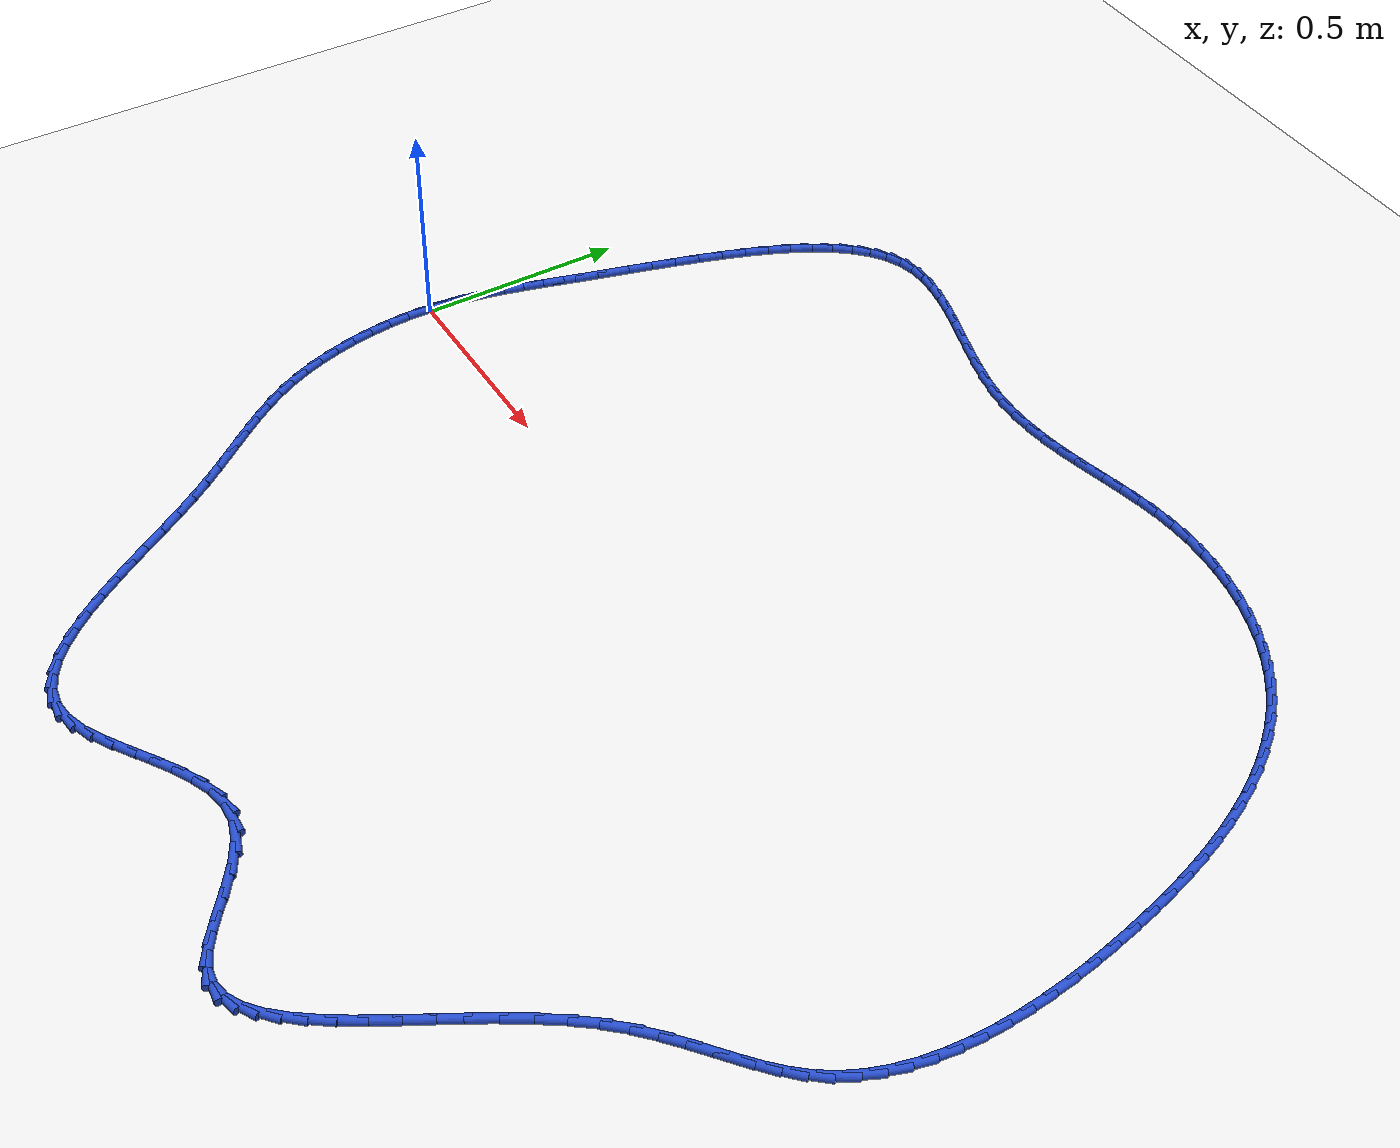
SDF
<sdf version="1.6">
 <world name="default">
  <light name="sun" type="directional">
   <pose>0 0 10 0 -0 0</pose>
   <diffuse>0.8 0.8 0.8 1</diffuse>
   <specular>0.2 0.2 0.2 1</specular>
   <attenuation>
    <range>1000</range>
    <constant>0.9</constant>
    <linear>0.01</linear>
    <quadratic>0.001</quadratic>
   </attenuation>
   <direction>-0.5 0.1 -0.9</direction>
  </light>
  <model name="ground_plane">
   <static>1</static>
   <link name="link">
    <collision name="collision">
     <geometry><plane><normal>0 0 1</normal><size>100 100</size></plane></geometry>
     <surface><friction><ode><mu>100</mu><mu2>50</mu2></ode></friction></surface>
    </collision>
    <visual name="visual">
     <cast_shadows>0</cast_shadows>
     <geometry><plane><normal>0 0 1</normal><size>100 100</size></plane></geometry>
     <material>
      <script><uri>file://media/materials/scripts/gazebo.material</uri><name>Gazebo/WhiteGlow</name></script>
     </material>
    </visual>
   </link>
  </model>
  <gravity>0 0 -9.8</gravity>
  <magnetic_field>6e-06 2.3e-05 -4.2e-05</magnetic_field>
  <atmosphere type="adiabatic"/>
  <physics name="default_physics" default="0" type="ode">
   <max_step_size>0.001</max_step_size>
   <real_time_factor>1</real_time_factor>
   <real_time_update_rate>1000</real_time_update_rate>
  </physics>
  <scene><ambient>0.4 0.4 0.4 1</ambient><background>0.7 0.7 0.7 1</background><shadows>1</shadows></scene>
  <spherical_coordinates>
   <surface_model>EARTH_WGS84</surface_model>
   <latitude_deg>0</latitude_deg>
   <longitude_deg>0</longitude_deg>
   <elevation>0</elevation>
   <heading_deg>0</heading_deg>
  </spherical_coordinates>
  <model name="line">
   <link name="link_0">
    <pose>3.122502256758253e-17 -4.163336342344337e-17 0.01 0 1.57 1.5024349348868296</pose>
    <collision name="collision">
     <geometry><cylinder><radius>0.01</radius><length>0.08</length></cylinder></geometry>
    </collision>
    <visual name="visual">
     <material>
      <script><name>Gazebo/Blue</name><uri>file://media/materials/scripts/gazebo.material</uri></script>
     </material>
     <geometry><cylinder><radius>0.01</radius><length>0.08</length></cylinder></geometry>
    </visual>
   </link>
   <link name="link_1">
    <pose>0.0034064838489011695 0.049752873892944895 0.01 0 1.57 1.444446069055366</pose>
    <collision name="collision">
     <geometry><cylinder><radius>0.01</radius><length>0.08</length></cylinder></geometry>
    </collision>
    <visual name="visual">
     <material>
      <script><name>Gazebo/Blue</name><uri>file://media/materials/scripts/gazebo.material</uri></script>
     </material>
     <geometry><cylinder><radius>0.01</radius><length>0.08</length></cylinder></geometry>
    </visual>
   </link>
   <link name="link_2">
    <pose>0.009621208689857526 0.0986773341577474 0.01 0 1.57 1.3946409832740725</pose>
    <collision name="collision">
     <geometry><cylinder><radius>0.01</radius><length>0.08</length></cylinder></geometry>
    </collision>
    <visual name="visual">
     <material>
      <script><name>Gazebo/Blue</name><uri>file://media/materials/scripts/gazebo.material</uri></script>
     </material>
     <geometry><cylinder><radius>0.01</radius><length>0.08</length></cylinder></geometry>
    </visual>
   </link>
   <link name="link_3">
    <pose>0.018259850518929966 0.14720894199530554 0.01 0 1.57 1.3544053752930096</pose>
    <collision name="collision">
     <geometry><cylinder><radius>0.01</radius><length>0.08</length></cylinder></geometry>
    </collision>
    <visual name="visual">
     <material>
      <script><name>Gazebo/Blue</name><uri>file://media/materials/scripts/gazebo.material</uri></script>
     </material>
     <geometry><cylinder><radius>0.01</radius><length>0.08</length></cylinder></geometry>
    </visual>
   </link>
   <link name="link_4">
    <pose>0.028938085332179397 0.19578325860651738 0.01 0 1.57 1.3244681709011066</pose>
    <collision name="collision">
     <geometry><cylinder><radius>0.01</radius><length>0.08</length></cylinder></geometry>
    </collision>
    <visual name="visual">
     <material>
      <script><name>Gazebo/Blue</name><uri>file://media/materials/scripts/gazebo.material</uri></script>
     </material>
     <geometry><cylinder><radius>0.01</radius><length>0.08</length></cylinder></geometry>
    </visual>
   </link>
   <link name="link_5">
    <pose>0.041271589125666676 0.2448358451922809 0.01 0 1.57 1.3049682244123708</pose>
    <collision name="collision">
     <geometry><cylinder><radius>0.01</radius><length>0.08</length></cylinder></geometry>
    </collision>
    <visual name="visual">
     <material>
      <script><name>Gazebo/Blue</name><uri>file://media/materials/scripts/gazebo.material</uri></script>
     </material>
     <geometry><cylinder><radius>0.01</radius><length>0.08</length></cylinder></geometry>
    </visual>
   </link>
   <link name="link_6">
    <pose>0.054876037895452756 0.29480226295349454 0.01 0 1.57 1.2955727894526858</pose>
    <collision name="collision">
     <geometry><cylinder><radius>0.01</radius><length>0.08</length></cylinder></geometry>
    </collision>
    <visual name="visual">
     <material>
      <script><name>Gazebo/Blue</name><uri>file://media/materials/scripts/gazebo.material</uri></script>
     </material>
     <geometry><cylinder><radius>0.01</radius><length>0.08</length></cylinder></geometry>
    </visual>
   </link>
   <link name="link_7">
    <pose>0.06936710763759844 0.3461180730910558 0.01 0 1.57 1.2956034167263761</pose>
    <collision name="collision">
     <geometry><cylinder><radius>0.01</radius><length>0.08</length></cylinder></geometry>
    </collision>
    <visual name="visual">
     <material>
      <script><name>Gazebo/Blue</name><uri>file://media/materials/scripts/gazebo.material</uri></script>
     </material>
     <geometry><cylinder><radius>0.01</radius><length>0.08</length></cylinder></geometry>
    </visual>
   </link>
   <link name="link_8">
    <pose>0.08436047434816471 0.3992188368058633 0.01 0 1.57 1.3025343453050016</pose>
    <collision name="collision">
     <geometry><cylinder><radius>0.01</radius><length>0.08</length></cylinder></geometry>
    </collision>
    <visual name="visual">
     <material>
      <script><name>Gazebo/Blue</name><uri>file://media/materials/scripts/gazebo.material</uri></script>
     </material>
     <geometry><cylinder><radius>0.01</radius><length>0.08</length></cylinder></geometry>
    </visual>
   </link>
   <link name="link_9">
    <pose>0.09953490346010475 0.45442108319089597 0.01 0 1.57 1.3061589064330774</pose>
    <collision name="collision">
     <geometry><cylinder><radius>0.01</radius><length>0.08</length></cylinder></geometry>
    </collision>
    <visual name="visual">
     <material>
      <script><name>Gazebo/Blue</name><uri>file://media/materials/scripts/gazebo.material</uri></script>
     </material>
     <geometry><cylinder><radius>0.01</radius><length>0.08</length></cylinder></geometry>
    </visual>
   </link>
   <link name="link_10">
    <pose>0.11495323499113344 0.5113167001048133 0.01 0 1.57 1.3033156665192283</pose>
    <collision name="collision">
     <geometry><cylinder><radius>0.01</radius><length>0.08</length></cylinder></geometry>
    </collision>
    <visual name="visual">
     <material>
      <script><name>Gazebo/Blue</name><uri>file://media/materials/scripts/gazebo.material</uri></script>
     </material>
     <geometry><cylinder><radius>0.01</radius><length>0.08</length></cylinder></geometry>
    </visual>
   </link>
   <link name="link_11">
    <pose>0.13082284048837703 0.5692248848664 0.01 0 1.57 1.294264903463488</pose>
    <collision name="collision">
     <geometry><cylinder><radius>0.01</radius><length>0.08</length></cylinder></geometry>
    </collision>
    <visual name="visual">
     <material>
      <script><name>Gazebo/Blue</name><uri>file://media/materials/scripts/gazebo.material</uri></script>
     </material>
     <geometry><cylinder><radius>0.01</radius><length>0.08</length></cylinder></geometry>
    </visual>
   </link>
   <link name="link_12">
    <pose>0.14735135341848737 0.6274643406256109 0.01 0 1.57 1.2788922850609503</pose>
    <collision name="collision">
     <geometry><cylinder><radius>0.01</radius><length>0.08</length></cylinder></geometry>
    </collision>
    <visual name="visual">
     <material>
      <script><name>Gazebo/Blue</name><uri>file://media/materials/scripts/gazebo.material</uri></script>
     </material>
     <geometry><cylinder><radius>0.01</radius><length>0.08</length></cylinder></geometry>
    </visual>
   </link>
   <link name="link_13">
    <pose>0.16474640724811632 0.6853537705324002 0.01 0 1.57 1.2567180476974975</pose>
    <collision name="collision">
     <geometry><cylinder><radius>0.01</radius><length>0.08</length></cylinder></geometry>
    </collision>
    <visual name="visual">
     <material>
      <script><name>Gazebo/Blue</name><uri>file://media/materials/scripts/gazebo.material</uri></script>
     </material>
     <geometry><cylinder><radius>0.01</radius><length>0.08</length></cylinder></geometry>
    </visual>
   </link>
   <link name="link_14">
    <pose>0.18321563544391575 0.7422118777367221 0.01 0 1.57 1.2268685357178266</pose>
    <collision name="collision">
     <geometry><cylinder><radius>0.01</radius><length>0.08</length></cylinder></geometry>
    </collision>
    <visual name="visual">
     <material>
      <script><name>Gazebo/Blue</name><uri>file://media/materials/scripts/gazebo.material</uri></script>
     </material>
     <geometry><cylinder><radius>0.01</radius><length>0.08</length></cylinder></geometry>
    </visual>
   </link>
   <link name="link_15">
    <pose>0.2029666714725374 0.7973573653885311 0.01 0 1.57 1.1880066240494118</pose>
    <collision name="collision">
     <geometry><cylinder><radius>0.01</radius><length>0.08</length></cylinder></geometry>
    </collision>
    <visual name="visual">
     <material>
      <script><name>Gazebo/Blue</name><uri>file://media/materials/scripts/gazebo.material</uri></script>
     </material>
     <geometry><cylinder><radius>0.01</radius><length>0.08</length></cylinder></geometry>
    </visual>
   </link>
   <link name="link_16">
    <pose>0.22420714880063325 0.8501089366377819 0.01 0 1.57 1.1382225743775571</pose>
    <collision name="collision">
     <geometry><cylinder><radius>0.01</radius><length>0.08</length></cylinder></geometry>
    </collision>
    <visual name="visual">
     <material>
      <script><name>Gazebo/Blue</name><uri>file://media/materials/scripts/gazebo.material</uri></script>
     </material>
     <geometry><cylinder><radius>0.01</radius><length>0.08</length></cylinder></geometry>
    </visual>
   </link>
   <link name="link_17">
    <pose>0.2471447008948551 0.8997852946344284 0.01 0 1.57 1.0748955111268819</pose>
    <collision name="collision">
     <geometry><cylinder><radius>0.01</radius><length>0.08</length></cylinder></geometry>
    </collision>
    <visual name="visual">
     <material>
      <script><name>Gazebo/Blue</name><uri>file://media/materials/scripts/gazebo.material</uri></script>
     </material>
     <geometry><cylinder><radius>0.01</radius><length>0.08</length></cylinder></geometry>
    </visual>
   </link>
   <link name="link_18">
    <pose>0.27198696122185484 0.9457051425284254 0.01 0 1.57 0.9945689741852937</pose>
    <collision name="collision">
     <geometry><cylinder><radius>0.01</radius><length>0.08</length></cylinder></geometry>
    </collision>
    <visual name="visual">
     <material>
      <script><name>Gazebo/Blue</name><uri>file://media/materials/scripts/gazebo.material</uri></script>
     </material>
     <geometry><cylinder><radius>0.01</radius><length>0.08</length></cylinder></geometry>
    </visual>
   </link>
   <link name="link_19">
    <pose>0.29894156324828436 0.9871871834697274 0.01 0 1.57 0.8929737704911271</pose>
    <collision name="collision">
     <geometry><cylinder><radius>0.01</radius><length>0.08</length></cylinder></geometry>
    </collision>
    <visual name="visual">
     <material>
      <script><name>Gazebo/Blue</name><uri>file://media/materials/scripts/gazebo.material</uri></script>
     </material>
     <geometry><cylinder><radius>0.01</radius><length>0.08</length></cylinder></geometry>
    </visual>
   </link>
   <link name="link_20">
    <pose>0.3282161404407952 1.0235501206082882 0.01 0 1.57 0.7655233677494663</pose>
    <collision name="collision">
     <geometry><cylinder><radius>0.01</radius><length>0.08</length></cylinder></geometry>
    </collision>
    <visual name="visual">
     <material>
      <script><name>Gazebo/Blue</name><uri>file://media/materials/scripts/gazebo.material</uri></script>
     </material>
     <geometry><cylinder><radius>0.01</radius><length>0.08</length></cylinder></geometry>
    </visual>
   </link>
   <link name="link_21">
    <pose>0.3600183262660398 1.0541126570940633 0.01 0 1.57 0.6088704865778769</pose>
    <collision name="collision">
     <geometry><cylinder><radius>0.01</radius><length>0.08</length></cylinder></geometry>
    </collision>
    <visual name="visual">
     <material>
      <script><name>Gazebo/Blue</name><uri>file://media/materials/scripts/gazebo.material</uri></script>
     </material>
     <geometry><cylinder><radius>0.01</radius><length>0.08</length></cylinder></geometry>
    </visual>
   </link>
   <link name="link_22">
    <pose>0.39455575419066935 1.0781934960770059 0.01 0 1.57 0.42400061528859134</pose>
    <collision name="collision">
     <geometry><cylinder><radius>0.01</radius><length>0.08</length></cylinder></geometry>
    </collision>
    <visual name="visual">
     <material>
      <script><name>Gazebo/Blue</name><uri>file://media/materials/scripts/gazebo.material</uri></script>
     </material>
     <geometry><cylinder><radius>0.01</radius><length>0.08</length></cylinder></geometry>
    </visual>
   </link>
   <link name="link_23">
    <pose>0.4320360576813361 1.0951113407070712 0.01 0 1.57 0.22089250144606867</pose>
    <collision name="collision">
     <geometry><cylinder><radius>0.01</radius><length>0.08</length></cylinder></geometry>
    </collision>
    <visual name="visual">
     <material>
      <script><name>Gazebo/Blue</name><uri>file://media/materials/scripts/gazebo.material</uri></script>
     </material>
     <geometry><cylinder><radius>0.01</radius><length>0.08</length></cylinder></geometry>
    </visual>
   </link>
   <link name="link_24">
    <pose>0.47265217463178716 1.104231963536984 0.01 0 1.57 0.03800374693829767</pose>
    <collision name="collision">
     <geometry><cylinder><radius>0.01</radius><length>0.08</length></cylinder></geometry>
    </collision>
    <visual name="visual">
     <material>
      <script><name>Gazebo/Blue</name><uri>file://media/materials/scripts/gazebo.material</uri></script>
     </material>
     <geometry><cylinder><radius>0.01</radius><length>0.08</length></cylinder></geometry>
    </visual>
   </link>
   <link name="link_25">
    <pose>0.5162941411966497 1.1058913207285803 0.01 0 1.57 -0.09810788513666562</pose>
    <collision name="collision">
     <geometry><cylinder><radius>0.01</radius><length>0.08</length></cylinder></geometry>
    </collision>
    <visual name="visual">
     <material>
      <script><name>Gazebo/Blue</name><uri>file://media/materials/scripts/gazebo.material</uri></script>
     </material>
     <geometry><cylinder><radius>0.01</radius><length>0.08</length></cylinder></geometry>
    </visual>
   </link>
   <link name="link_26">
    <pose>0.5625673948369634 1.1013369280421808 0.01 0 1.57 -0.193139433856809</pose>
    <collision name="collision">
     <geometry><cylinder><radius>0.01</radius><length>0.08</length></cylinder></geometry>
    </collision>
    <visual name="visual">
     <material>
      <script><name>Gazebo/Blue</name><uri>file://media/materials/scripts/gazebo.material</uri></script>
     </material>
     <geometry><cylinder><radius>0.01</radius><length>0.08</length></cylinder></geometry>
    </visual>
   </link>
   <link name="link_27">
    <pose>0.611066342508502 1.091851631558232 0.01 0 1.57 -0.2553060456188679</pose>
    <collision name="collision">
     <geometry><cylinder><radius>0.01</radius><length>0.08</length></cylinder></geometry>
    </collision>
    <visual name="visual">
     <material>
      <script><name>Gazebo/Blue</name><uri>file://media/materials/scripts/gazebo.material</uri></script>
     </material>
     <geometry><cylinder><radius>0.01</radius><length>0.08</length></cylinder></geometry>
    </visual>
   </link>
   <link name="link_28">
    <pose>0.6613853911670386 1.0787182773571802 0.01 0 1.57 -0.2910754544736426</pose>
    <collision name="collision">
     <geometry><cylinder><radius>0.01</radius><length>0.08</length></cylinder></geometry>
    </collision>
    <visual name="visual">
     <material>
      <script><name>Gazebo/Blue</name><uri>file://media/materials/scripts/gazebo.material</uri></script>
     </material>
     <geometry><cylinder><radius>0.01</radius><length>0.08</length></cylinder></geometry>
    </visual>
   </link>
   <link name="link_29">
    <pose>0.7131189477683475 1.0632197115194713 0.01 0 1.57 -0.3045924322972704</pose>
    <collision name="collision">
     <geometry><cylinder><radius>0.01</radius><length>0.08</length></cylinder></geometry>
    </collision>
    <visual name="visual">
     <material>
      <script><name>Gazebo/Blue</name><uri>file://media/materials/scripts/gazebo.material</uri></script>
     </material>
     <geometry><cylinder><radius>0.01</radius><length>0.08</length></cylinder></geometry>
    </visual>
   </link>
   <link name="link_30">
    <pose>0.7658614192682015 1.0466387801255517 0.01 0 1.57 -0.2979227758545524</pose>
    <collision name="collision">
     <geometry><cylinder><radius>0.01</radius><length>0.08</length></cylinder></geometry>
    </collision>
    <visual name="visual">
     <material>
      <script><name>Gazebo/Blue</name><uri>file://media/materials/scripts/gazebo.material</uri></script>
     </material>
     <geometry><cylinder><radius>0.01</radius><length>0.08</length></cylinder></geometry>
    </visual>
   </link>
   <link name="link_31">
    <pose>0.8192072126223747 1.0302583292558676 0.01 0 1.57 -0.2713616040444545</pose>
    <collision name="collision">
     <geometry><cylinder><radius>0.01</radius><length>0.08</length></cylinder></geometry>
    </collision>
    <visual name="visual">
     <material>
      <script><name>Gazebo/Blue</name><uri>file://media/materials/scripts/gazebo.material</uri></script>
     </material>
     <geometry><cylinder><radius>0.01</radius><length>0.08</length></cylinder></geometry>
    </visual>
   </link>
   <link name="link_32">
    <pose>0.8727507347866399 1.0153612049908654 0.01 0 1.57 -0.22364081399501537</pose>
    <collision name="collision">
     <geometry><cylinder><radius>0.01</radius><length>0.08</length></cylinder></geometry>
    </collision>
    <visual name="visual">
     <material>
      <script><name>Gazebo/Blue</name><uri>file://media/materials/scripts/gazebo.material</uri></script>
     </material>
     <geometry><cylinder><radius>0.01</radius><length>0.08</length></cylinder></geometry>
    </visual>
   </link>
   <link name="link_33">
    <pose>0.9260863927167708 1.0032302534109907 0.01 0 1.57 -0.15231245798812665</pose>
    <collision name="collision">
     <geometry><cylinder><radius>0.01</radius><length>0.08</length></cylinder></geometry>
    </collision>
    <visual name="visual">
     <material>
      <script><name>Gazebo/Blue</name><uri>file://media/materials/scripts/gazebo.material</uri></script>
     </material>
     <geometry><cylinder><radius>0.01</radius><length>0.08</length></cylinder></geometry>
    </visual>
   </link>
   <link name="link_34">
    <pose>0.9788118989345896 0.9951368181853478 0.01 0 1.57 -0.06693519968694818</pose>
    <collision name="collision">
     <geometry><cylinder><radius>0.01</radius><length>0.08</length></cylinder></geometry>
    </collision>
    <visual name="visual">
     <material>
      <script><name>Gazebo/Blue</name><uri>file://media/materials/scripts/gazebo.material</uri></script>
     </material>
     <geometry><cylinder><radius>0.01</radius><length>0.08</length></cylinder></geometry>
    </visual>
   </link>
   <link name="link_35">
    <pose>1.0307248174096666 0.9916568178951465 0.01 0 1.57 0.01227071794901337</pose>
    <collision name="collision">
     <geometry><cylinder><radius>0.01</radius><length>0.08</length></cylinder></geometry>
    </collision>
    <visual name="visual">
     <material>
      <script><name>Gazebo/Blue</name><uri>file://media/materials/scripts/gazebo.material</uri></script>
     </material>
     <geometry><cylinder><radius>0.01</radius><length>0.08</length></cylinder></geometry>
    </visual>
   </link>
   <link name="link_36">
    <pose>1.081933357574416 0.9922852149877642 0.01 0 1.57 0.08154232920392279</pose>
    <collision name="collision">
     <geometry><cylinder><radius>0.01</radius><length>0.08</length></cylinder></geometry>
    </collision>
    <visual name="visual">
     <material>
      <script><name>Gazebo/Blue</name><uri>file://media/materials/scripts/gazebo.material</uri></script>
     </material>
     <geometry><cylinder><radius>0.01</radius><length>0.08</length></cylinder></geometry>
    </visual>
   </link>
   <link name="link_37">
    <pose>1.1325725536657614 0.9964236293691815 0.01 0 1.57 0.13951334153947184</pose>
    <collision name="collision">
     <geometry><cylinder><radius>0.01</radius><length>0.08</length></cylinder></geometry>
    </collision>
    <visual name="visual">
     <material>
      <script><name>Gazebo/Blue</name><uri>file://media/materials/scripts/gazebo.material</uri></script>
     </material>
     <geometry><cylinder><radius>0.01</radius><length>0.08</length></cylinder></geometry>
    </visual>
   </link>
   <link name="link_38">
    <pose>1.1827774399206277 1.0034736809453788 0.01 0 1.57 0.18481311294472316</pose>
    <collision name="collision">
     <geometry><cylinder><radius>0.01</radius><length>0.08</length></cylinder></geometry>
    </collision>
    <visual name="visual">
     <material>
      <script><name>Gazebo/Blue</name><uri>file://media/materials/scripts/gazebo.material</uri></script>
     </material>
     <geometry><cylinder><radius>0.01</radius><length>0.08</length></cylinder></geometry>
    </visual>
   </link>
   <link name="link_39">
    <pose>1.2326858865196098 1.0128038861425124 0.01 0 1.57 0.21310270665090636</pose>
    <collision name="collision">
     <geometry><cylinder><radius>0.01</radius><length>0.08</length></cylinder></geometry>
    </collision>
    <visual name="visual">
     <material>
      <script><name>Gazebo/Blue</name><uri>file://media/materials/scripts/gazebo.material</uri></script>
     </material>
     <geometry><cylinder><radius>0.01</radius><length>0.08</length></cylinder></geometry>
    </visual>
   </link>
   <link name="link_40">
    <pose>1.2824537283065853 1.023573062980368 0.01 0 1.57 0.22288784067027426</pose>
    <collision name="collision">
     <geometry><cylinder><radius>0.01</radius><length>0.08</length></cylinder></geometry>
    </collision>
    <visual name="visual">
     <material>
      <script><name>Gazebo/Blue</name><uri>file://media/materials/scripts/gazebo.material</uri></script>
     </material>
     <geometry><cylinder><radius>0.01</radius><length>0.08</length></cylinder></geometry>
    </visual>
   </link>
   <link name="link_41">
    <pose>1.3322438132164283 1.0348581668808963 0.01 0 1.57 0.21432103683781775</pose>
    <collision name="collision">
     <geometry><cylinder><radius>0.01</radius><length>0.08</length></cylinder></geometry>
    </collision>
    <visual name="visual">
     <material>
      <script><name>Gazebo/Blue</name><uri>file://media/materials/scripts/gazebo.material</uri></script>
     </material>
     <geometry><cylinder><radius>0.01</radius><length>0.08</length></cylinder></geometry>
    </visual>
   </link>
   <link name="link_42">
    <pose>1.382219005232821 1.0457359659310619 0.01 0 1.57 0.18749076358438954</pose>
    <collision name="collision">
     <geometry><cylinder><radius>0.01</radius><length>0.08</length></cylinder></geometry>
    </collision>
    <visual name="visual">
     <material>
      <script><name>Gazebo/Blue</name><uri>file://media/materials/scripts/gazebo.material</uri></script>
     </material>
     <geometry><cylinder><radius>0.01</radius><length>0.08</length></cylinder></geometry>
    </visual>
   </link>
   <link name="link_43">
    <pose>1.4325421683394453 1.0552832282178308 0.01 0 1.57 0.14250415444637676</pose>
    <collision name="collision">
     <geometry><cylinder><radius>0.01</radius><length>0.08</length></cylinder></geometry>
    </collision>
    <visual name="visual">
     <material>
      <script><name>Gazebo/Blue</name><uri>file://media/materials/scripts/gazebo.material</uri></script>
     </material>
     <geometry><cylinder><radius>0.01</radius><length>0.08</length></cylinder></geometry>
    </visual>
   </link>
   <link name="link_44">
    <pose>1.483376166519985 1.0625767218281688 0.01 0 1.57 0.0799822787415558</pose>
    <collision name="collision">
     <geometry><cylinder><radius>0.01</radius><length>0.08</length></cylinder></geometry>
    </collision>
    <visual name="visual">
     <material>
      <script><name>Gazebo/Blue</name><uri>file://media/materials/scripts/gazebo.material</uri></script>
     </material>
     <geometry><cylinder><radius>0.01</radius><length>0.08</length></cylinder></geometry>
    </visual>
   </link>
   <link name="link_45">
    <pose>1.5348772894511034 1.0667047052177914 0.01 0 1.57 0.008994929706711395</pose>
    <collision name="collision">
     <geometry><cylinder><radius>0.01</radius><length>0.08</length></cylinder></geometry>
    </collision>
    <visual name="visual">
     <material>
      <script><name>Gazebo/Blue</name><uri>file://media/materials/scripts/gazebo.material</uri></script>
     </material>
     <geometry><cylinder><radius>0.01</radius><length>0.08</length></cylinder></geometry>
    </visual>
   </link>
   <link name="link_46">
    <pose>1.5869627869559528 1.0671732232423923 0.01 0 1.57 -0.06033186394168268</pose>
    <collision name="collision">
     <geometry><cylinder><radius>0.01</radius><length>0.08</length></cylinder></geometry>
    </collision>
    <visual name="visual">
     <material>
      <script><name>Gazebo/Blue</name><uri>file://media/materials/scripts/gazebo.material</uri></script>
     </material>
     <geometry><cylinder><radius>0.01</radius><length>0.08</length></cylinder></geometry>
    </visual>
   </link>
   <link name="link_47">
    <pose>1.6392486291988257 1.0640148879481006 0.01 0 1.57 -0.12829653611474545</pose>
    <collision name="collision">
     <geometry><cylinder><radius>0.01</radius><length>0.08</length></cylinder></geometry>
    </collision>
    <visual name="visual">
     <material>
      <script><name>Gazebo/Blue</name><uri>file://media/materials/scripts/gazebo.material</uri></script>
     </material>
     <geometry><cylinder><radius>0.01</radius><length>0.08</length></cylinder></geometry>
    </visual>
   </link>
   <link name="link_48">
    <pose>1.691331554742499 1.05729592377431 0.01 0 1.57 -0.1958637644436021</pose>
    <collision name="collision">
     <geometry><cylinder><radius>0.01</radius><length>0.08</length></cylinder></geometry>
    </collision>
    <visual name="visual">
     <material>
      <script><name>Gazebo/Blue</name><uri>file://media/materials/scripts/gazebo.material</uri></script>
     </material>
     <geometry><cylinder><radius>0.01</radius><length>0.08</length></cylinder></geometry>
    </visual>
   </link>
   <link name="link_49">
    <pose>1.7428083021497507 1.0470825551604133 0.01 0 1.57 -0.263995774439734</pose>
    <collision name="collision">
     <geometry><cylinder><radius>0.01</radius><length>0.08</length></cylinder></geometry>
    </collision>
    <visual name="visual">
     <material>
      <script><name>Gazebo/Blue</name><uri>file://media/materials/scripts/gazebo.material</uri></script>
     </material>
     <geometry><cylinder><radius>0.01</radius><length>0.08</length></cylinder></geometry>
    </visual>
   </link>
   <link name="link_50">
    <pose>1.7932756099833596 1.0334410065458048 0.01 0 1.57 -0.33366408940121034</pose>
    <collision name="collision">
     <geometry><cylinder><radius>0.01</radius><length>0.08</length></cylinder></geometry>
    </collision>
    <visual name="visual">
     <material>
      <script><name>Gazebo/Blue</name><uri>file://media/materials/scripts/gazebo.material</uri></script>
     </material>
     <geometry><cylinder><radius>0.01</radius><length>0.08</length></cylinder></geometry>
    </visual>
   </link>
   <link name="link_51">
    <pose>1.8423302168061024 1.0164375023698775 0.01 0 1.57 -0.40585895835611846</pose>
    <collision name="collision">
     <geometry><cylinder><radius>0.01</radius><length>0.08</length></cylinder></geometry>
    </collision>
    <visual name="visual">
     <material>
      <script><name>Gazebo/Blue</name><uri>file://media/materials/scripts/gazebo.material</uri></script>
     </material>
     <geometry><cylinder><radius>0.01</radius><length>0.08</length></cylinder></geometry>
    </visual>
   </link>
   <link name="link_52">
    <pose>1.8895688611807573 0.9961382670720247 0.01 0 1.57 -0.4815915034889797</pose>
    <collision name="collision">
     <geometry><cylinder><radius>0.01</radius><length>0.08</length></cylinder></geometry>
    </collision>
    <visual name="visual">
     <material>
      <script><name>Gazebo/Blue</name><uri>file://media/materials/scripts/gazebo.material</uri></script>
     </material>
     <geometry><cylinder><radius>0.01</radius><length>0.08</length></cylinder></geometry>
    </visual>
   </link>
   <link name="link_53">
    <pose>1.9345882816701017 0.9726095250916403 0.01 0 1.57 -0.5616455412536447</pose>
    <collision name="collision">
     <geometry><cylinder><radius>0.01</radius><length>0.08</length></cylinder></geometry>
    </collision>
    <visual name="visual">
     <material>
      <script><name>Gazebo/Blue</name><uri>file://media/materials/scripts/gazebo.material</uri></script>
     </material>
     <geometry><cylinder><radius>0.01</radius><length>0.08</length></cylinder></geometry>
    </visual>
   </link>
   <link name="link_54">
    <pose>1.9770024676930367 0.9459206423492413 0.01 0 1.57 -0.6428294610637665</pose>
    <collision name="collision">
     <geometry><cylinder><radius>0.01</radius><length>0.08</length></cylinder></geometry>
    </collision>
    <visual name="visual">
     <material>
      <script><name>Gazebo/Blue</name><uri>file://media/materials/scripts/gazebo.material</uri></script>
     </material>
     <geometry><cylinder><radius>0.01</radius><length>0.08</length></cylinder></geometry>
    </visual>
   </link>
   <link name="link_55">
    <pose>2.0166980057784474 0.9161906262828136 0.01 0 1.57 -0.7213701250407571</pose>
    <collision name="collision">
     <geometry><cylinder><radius>0.01</radius><length>0.08</length></cylinder></geometry>
    </collision>
    <visual name="visual">
     <material>
      <script><name>Gazebo/Blue</name><uri>file://media/materials/scripts/gazebo.material</uri></script>
     </material>
     <geometry><cylinder><radius>0.01</radius><length>0.08</length></cylinder></geometry>
    </visual>
   </link>
   <link name="link_56">
    <pose>2.05377898596823 0.8835780929837168 0.01 0 1.57 -0.7962508761750118</pose>
    <collision name="collision">
     <geometry><cylinder><radius>0.01</radius><length>0.08</length></cylinder></geometry>
    </collision>
    <visual name="visual">
     <material>
      <script><name>Gazebo/Blue</name><uri>file://media/materials/scripts/gazebo.material</uri></script>
     </material>
     <geometry><cylinder><radius>0.01</radius><length>0.08</length></cylinder></geometry>
    </visual>
   </link>
   <link name="link_57">
    <pose>2.0883555540625554 0.8482427613320759 0.01 0 1.57 -0.8667826615746277</pose>
    <collision name="collision">
     <geometry><cylinder><radius>0.01</radius><length>0.08</length></cylinder></geometry>
    </collision>
    <visual name="visual">
     <material>
      <script><name>Gazebo/Blue</name><uri>file://media/materials/scripts/gazebo.material</uri></script>
     </material>
     <geometry><cylinder><radius>0.01</radius><length>0.08</length></cylinder></geometry>
    </visual>
   </link>
   <link name="link_58">
    <pose>2.120537855861596 0.8103443502080152 0.01 0 1.57 -0.932526662512129</pose>
    <collision name="collision">
     <geometry><cylinder><radius>0.01</radius><length>0.08</length></cylinder></geometry>
    </collision>
    <visual name="visual">
     <material>
      <script><name>Gazebo/Blue</name><uri>file://media/materials/scripts/gazebo.material</uri></script>
     </material>
     <geometry><cylinder><radius>0.01</radius><length>0.08</length></cylinder></geometry>
    </visual>
   </link>
   <link name="link_59">
    <pose>2.150436037165523 0.7700425784916601 0.01 0 1.57 -0.9932704989369299</pose>
    <collision name="collision">
     <geometry><cylinder><radius>0.01</radius><length>0.08</length></cylinder></geometry>
    </collision>
    <visual name="visual">
     <material>
      <script><name>Gazebo/Blue</name><uri>file://media/materials/scripts/gazebo.material</uri></script>
     </material>
     <geometry><cylinder><radius>0.01</radius><length>0.08</length></cylinder></geometry>
    </visual>
   </link>
   <link name="link_60">
    <pose>2.17816024377451 0.7274971650631356 0.01 0 1.57 -1.0489871485948696</pose>
    <collision name="collision">
     <geometry><cylinder><radius>0.01</radius><length>0.08</length></cylinder></geometry>
    </collision>
    <visual name="visual">
     <material>
      <script><name>Gazebo/Blue</name><uri>file://media/materials/scripts/gazebo.material</uri></script>
     </material>
     <geometry><cylinder><radius>0.01</radius><length>0.08</length></cylinder></geometry>
    </visual>
   </link>
   <link name="link_61">
    <pose>2.203820621488727 0.682867828802566 0.01 0 1.57 -1.0997879977297422</pose>
    <collision name="collision">
     <geometry><cylinder><radius>0.01</radius><length>0.08</length></cylinder></geometry>
    </collision>
    <visual name="visual">
     <material>
      <script><name>Gazebo/Blue</name><uri>file://media/materials/scripts/gazebo.material</uri></script>
     </material>
     <geometry><cylinder><radius>0.01</radius><length>0.08</length></cylinder></geometry>
    </visual>
   </link>
   <link name="link_62">
    <pose>2.227527316108347 0.6363142885900762 0.01 0 1.57 -1.1458782137169803</pose>
    <collision name="collision">
     <geometry><cylinder><radius>0.01</radius><length>0.08</length></cylinder></geometry>
    </collision>
    <visual name="visual">
     <material>
      <script><name>Gazebo/Blue</name><uri>file://media/materials/scripts/gazebo.material</uri></script>
     </material>
     <geometry><cylinder><radius>0.01</radius><length>0.08</length></cylinder></geometry>
    </visual>
   </link>
   <link name="link_63">
    <pose>2.249390473433541 0.5879962633057915 0.01 0 1.57 -1.1875189334384053</pose>
    <collision name="collision">
     <geometry><cylinder><radius>0.01</radius><length>0.08</length></cylinder></geometry>
    </collision>
    <visual name="visual">
     <material>
      <script><name>Gazebo/Blue</name><uri>file://media/materials/scripts/gazebo.material</uri></script>
     </material>
     <geometry><cylinder><radius>0.01</radius><length>0.08</length></cylinder></geometry>
    </visual>
   </link>
   <link name="link_64">
    <pose>2.2695202392644815 0.5380734718298367 0.01 0 1.57 -1.2249978007042315</pose>
    <collision name="collision">
     <geometry><cylinder><radius>0.01</radius><length>0.08</length></cylinder></geometry>
    </collision>
    <visual name="visual">
     <material>
      <script><name>Gazebo/Blue</name><uri>file://media/materials/scripts/gazebo.material</uri></script>
     </material>
     <geometry><cylinder><radius>0.01</radius><length>0.08</length></cylinder></geometry>
    </visual>
   </link>
   <link name="link_65">
    <pose>2.2880267594013404 0.4867056330423363 0.01 0 1.57 -1.2586075190022146</pose>
    <collision name="collision">
     <geometry><cylinder><radius>0.01</radius><length>0.08</length></cylinder></geometry>
    </collision>
    <visual name="visual">
     <material>
      <script><name>Gazebo/Blue</name><uri>file://media/materials/scripts/gazebo.material</uri></script>
     </material>
     <geometry><cylinder><radius>0.01</radius><length>0.08</length></cylinder></geometry>
    </visual>
   </link>
   <link name="link_66">
    <pose>2.305020179644288 0.43405246582341517 0.01 0 1.57 -1.2886311709031752</pose>
    <collision name="collision">
     <geometry><cylinder><radius>0.01</radius><length>0.08</length></cylinder></geometry>
    </collision>
    <visual name="visual">
     <material>
      <script><name>Gazebo/Blue</name><uri>file://media/materials/scripts/gazebo.material</uri></script>
     </material>
     <geometry><cylinder><radius>0.01</radius><length>0.08</length></cylinder></geometry>
    </visual>
   </link>
   <link name="link_67">
    <pose>2.3206106457934994 0.380273689053198 0.01 0 1.57 -1.3153327834618325</pose>
    <collision name="collision">
     <geometry><cylinder><radius>0.01</radius><length>0.08</length></cylinder></geometry>
    </collision>
    <visual name="visual">
     <material>
      <script><name>Gazebo/Blue</name><uri>file://media/materials/scripts/gazebo.material</uri></script>
     </material>
     <geometry><cylinder><radius>0.01</radius><length>0.08</length></cylinder></geometry>
    </visual>
   </link>
   <link name="link_68">
    <pose>2.3349083036491445 0.3255290216118105 0.01 0 1.57 -1.3389587395944422</pose>
    <collision name="collision">
     <geometry><cylinder><radius>0.01</radius><length>0.08</length></cylinder></geometry>
    </collision>
    <visual name="visual">
     <material>
      <script><name>Gazebo/Blue</name><uri>file://media/materials/scripts/gazebo.material</uri></script>
     </material>
     <geometry><cylinder><radius>0.01</radius><length>0.08</length></cylinder></geometry>
    </visual>
   </link>
   <link name="link_69">
    <pose>2.348022844187488 0.2699783604465285 0.01 0 1.57 -1.3614607573363913</pose>
    <collision name="collision">
     <geometry><cylinder><radius>0.01</radius><length>0.08</length></cylinder></geometry>
    </collision>
    <visual name="visual">
     <material>
      <script><name>Gazebo/Blue</name><uri>file://media/materials/scripts/gazebo.material</uri></script>
     </material>
     <geometry><cylinder><radius>0.01</radius><length>0.08</length></cylinder></geometry>
    </visual>
   </link>
   <link name="link_70">
    <pose>2.3599524545961432 0.21382525711860975 0.01 0 1.57 -1.3871331629922408</pose>
    <collision name="collision">
     <geometry><cylinder><radius>0.01</radius><length>0.08</length></cylinder></geometry>
    </collision>
    <visual name="visual">
     <material>
      <script><name>Gazebo/Blue</name><uri>file://media/materials/scripts/gazebo.material</uri></script>
     </material>
     <geometry><cylinder><radius>0.01</radius><length>0.08</length></cylinder></geometry>
    </visual>
   </link>
   <link name="link_71">
    <pose>2.370438693525881 0.15737373528848858 0.01 0 1.57 -1.4169937483911992</pose>
    <collision name="collision">
     <geometry><cylinder><radius>0.01</radius><length>0.08</length></cylinder></geometry>
    </collision>
    <visual name="visual">
     <material>
      <script><name>Gazebo/Blue</name><uri>file://media/materials/scripts/gazebo.material</uri></script>
     </material>
     <geometry><cylinder><radius>0.01</radius><length>0.08</length></cylinder></geometry>
    </visual>
   </link>
   <link name="link_72">
    <pose>2.379187146172139 0.1009419025085031 0.01 0 1.57 -1.4516315973730438</pose>
    <collision name="collision">
     <geometry><cylinder><radius>0.01</radius><length>0.08</length></cylinder></geometry>
    </collision>
    <visual name="visual">
     <material>
      <script><name>Gazebo/Blue</name><uri>file://media/materials/scripts/gazebo.material</uri></script>
     </material>
     <geometry><cylinder><radius>0.01</radius><length>0.08</length></cylinder></geometry>
    </visual>
   </link>
   <link name="link_73">
    <pose>2.385903397730353 0.04484786633099019 0.01 0 1.57 -1.4917803839875574</pose>
    <collision name="collision">
     <geometry><cylinder><radius>0.01</radius><length>0.08</length></cylinder></geometry>
    </collision>
    <visual name="visual">
     <material>
      <script><name>Gazebo/Blue</name><uri>file://media/materials/scripts/gazebo.material</uri></script>
     </material>
     <geometry><cylinder><radius>0.01</radius><length>0.08</length></cylinder></geometry>
    </visual>
   </link>
   <link name="link_74">
    <pose>2.390293033395962 -0.010590265691712937 0.01 0 1.57 -1.5383348880531529</pose>
    <collision name="collision">
     <geometry><cylinder><radius>0.01</radius><length>0.08</length></cylinder></geometry>
    </collision>
    <visual name="visual">
     <material>
      <script><name>Gazebo/Blue</name><uri>file://media/materials/scripts/gazebo.material</uri></script>
     </material>
     <geometry><cylinder><radius>0.01</radius><length>0.08</length></cylinder></geometry>
    </visual>
   </link>
   <link name="link_75">
    <pose>2.392061638364404 -0.06505438600726891 0.01 0 1.57 1.5492311661228946</pose>
    <collision name="collision">
     <geometry><cylinder><radius>0.01</radius><length>0.08</length></cylinder></geometry>
    </collision>
    <visual name="visual">
     <material>
      <script><name>Gazebo/Blue</name><uri>file://media/materials/scripts/gazebo.material</uri></script>
     </material>
     <geometry><cylinder><radius>0.01</radius><length>0.08</length></cylinder></geometry>
    </visual>
   </link>
   <link name="link_76">
    <pose>2.3909147978311163 -0.11822638706334088 0.01 0 1.57 1.48650176826832</pose>
    <collision name="collision">
     <geometry><cylinder><radius>0.01</radius><length>0.08</length></cylinder></geometry>
    </collision>
    <visual name="visual">
     <material>
      <script><name>Gazebo/Blue</name><uri>file://media/materials/scripts/gazebo.material</uri></script>
     </material>
     <geometry><cylinder><radius>0.01</radius><length>0.08</length></cylinder></geometry>
    </visual>
   </link>
   <link name="link_77">
    <pose>2.386558096991536 -0.1697881613075911 0.01 0 1.57 1.4137204018970764</pose>
    <collision name="collision">
     <geometry><cylinder><radius>0.01</radius><length>0.08</length></cylinder></geometry>
    </collision>
    <visual name="visual">
     <material>
      <script><name>Gazebo/Blue</name><uri>file://media/materials/scripts/gazebo.material</uri></script>
     </material>
     <geometry><cylinder><radius>0.01</radius><length>0.08</length></cylinder></geometry>
    </visual>
   </link>
   <link name="link_78">
    <pose>2.378697121041102 -0.2194216011876815 0.01 0 1.57 1.3295368613279976</pose>
    <collision name="collision">
     <geometry><cylinder><radius>0.01</radius><length>0.08</length></cylinder></geometry>
    </collision>
    <visual name="visual">
     <material>
      <script><name>Gazebo/Blue</name><uri>file://media/materials/scripts/gazebo.material</uri></script>
     </material>
     <geometry><cylinder><radius>0.01</radius><length>0.08</length></cylinder></geometry>
    </visual>
   </link>
   <link name="link_79">
    <pose>2.367037455175251 -0.2668085991512764 0.01 0 1.57 1.2328318999270813</pose>
    <collision name="collision">
     <geometry><cylinder><radius>0.01</radius><length>0.08</length></cylinder></geometry>
    </collision>
    <visual name="visual">
     <material>
      <script><name>Gazebo/Blue</name><uri>file://media/materials/scripts/gazebo.material</uri></script>
     </material>
     <geometry><cylinder><radius>0.01</radius><length>0.08</length></cylinder></geometry>
    </visual>
   </link>
   <link name="link_80">
    <pose>2.3512846845894213 -0.31163104764603705 0.01 0 1.57 1.123098271538699</pose>
    <collision name="collision">
     <geometry><cylinder><radius>0.01</radius><length>0.08</length></cylinder></geometry>
    </collision>
    <visual name="visual">
     <material>
      <script><name>Gazebo/Blue</name><uri>file://media/materials/scripts/gazebo.material</uri></script>
     </material>
     <geometry><cylinder><radius>0.01</radius><length>0.08</length></cylinder></geometry>
    </visual>
   </link>
   <link name="link_81">
    <pose>2.3311443944790504 -0.3535708391196275 0.01 0 1.57 1.000947719923357</pose>
    <collision name="collision">
     <geometry><cylinder><radius>0.01</radius><length>0.08</length></cylinder></geometry>
    </collision>
    <visual name="visual">
     <material>
      <script><name>Gazebo/Blue</name><uri>file://media/materials/scripts/gazebo.material</uri></script>
     </material>
     <geometry><cylinder><radius>0.01</radius><length>0.08</length></cylinder></geometry>
    </visual>
   </link>
   <link name="link_82">
    <pose>2.306322170039575 -0.3923098660197097 0.01 0 1.57 0.8753505238559841</pose>
    <collision name="collision">
     <geometry><cylinder><radius>0.01</radius><length>0.08</length></cylinder></geometry>
    </collision>
    <visual name="visual">
     <material>
      <script><name>Gazebo/Blue</name><uri>file://media/materials/scripts/gazebo.material</uri></script>
     </material>
     <geometry><cylinder><radius>0.01</radius><length>0.08</length></cylinder></geometry>
    </visual>
   </link>
   <link name="link_83">
    <pose>2.2767246121263267 -0.42777588265710836 0.01 0 1.57 0.7777896400408832</pose>
    <collision name="collision">
     <geometry><cylinder><radius>0.01</radius><length>0.08</length></cylinder></geometry>
    </collision>
    <visual name="visual">
     <material>
      <script><name>Gazebo/Blue</name><uri>file://media/materials/scripts/gazebo.material</uri></script>
     </material>
     <geometry><cylinder><radius>0.01</radius><length>0.08</length></cylinder></geometry>
    </visual>
   </link>
   <link name="link_84">
    <pose>2.243084865384659 -0.4609075874467572 0.01 0 1.57 0.7165369078485566</pose>
    <collision name="collision">
     <geometry><cylinder><radius>0.01</radius><length>0.08</length></cylinder></geometry>
    </collision>
    <visual name="visual">
     <material>
      <script><name>Gazebo/Blue</name><uri>file://media/materials/scripts/gazebo.material</uri></script>
     </material>
     <geometry><cylinder><radius>0.01</radius><length>0.08</length></cylinder></geometry>
    </visual>
   </link>
   <link name="link_85">
    <pose>2.206348486946992 -0.49290348010392565 0.01 0 1.57 0.6894393211643342</pose>
    <collision name="collision">
     <geometry><cylinder><radius>0.01</radius><length>0.08</length></cylinder></geometry>
    </collision>
    <visual name="visual">
     <material>
      <script><name>Gazebo/Blue</name><uri>file://media/materials/scripts/gazebo.material</uri></script>
     </material>
     <geometry><cylinder><radius>0.01</radius><length>0.08</length></cylinder></geometry>
    </visual>
   </link>
   <link name="link_86">
    <pose>2.167461034106219 -0.5249620605401646 0.01 0 1.57 0.6933966779392304</pose>
    <collision name="collision">
     <geometry><cylinder><radius>0.01</radius><length>0.08</length></cylinder></geometry>
    </collision>
    <visual name="visual">
     <material>
      <script><name>Gazebo/Blue</name><uri>file://media/materials/scripts/gazebo.material</uri></script>
     </material>
     <geometry><cylinder><radius>0.01</radius><length>0.08</length></cylinder></geometry>
    </visual>
   </link>
   <link name="link_87">
    <pose>2.1273680641552377 -0.5582818286670232 0.01 0 1.57 0.7253976206110584</pose>
    <collision name="collision">
     <geometry><cylinder><radius>0.01</radius><length>0.08</length></cylinder></geometry>
    </collision>
    <visual name="visual">
     <material>
      <script><name>Gazebo/Blue</name><uri>file://media/materials/scripts/gazebo.material</uri></script>
     </material>
     <geometry><cylinder><radius>0.01</radius><length>0.08</length></cylinder></geometry>
    </visual>
   </link>
   <link name="link_88">
    <pose>2.0870151343869434 -0.5940612843960512 0.01 0 1.57 0.7824945735420734</pose>
    <collision name="collision">
     <geometry><cylinder><radius>0.01</radius><length>0.08</length></cylinder></geometry>
    </collision>
    <visual name="visual">
     <material>
      <script><name>Gazebo/Blue</name><uri>file://media/materials/scripts/gazebo.material</uri></script>
     </material>
     <geometry><cylinder><radius>0.01</radius><length>0.08</length></cylinder></geometry>
    </visual>
   </link>
   <link name="link_89">
    <pose>2.0473478020942304 -0.6334989276387993 0.01 0 1.57 0.8606888353333896</pose>
    <collision name="collision">
     <geometry><cylinder><radius>0.01</radius><length>0.08</length></cylinder></geometry>
    </collision>
    <visual name="visual">
     <material>
      <script><name>Gazebo/Blue</name><uri>file://media/materials/scripts/gazebo.material</uri></script>
     </material>
     <geometry><cylinder><radius>0.01</radius><length>0.08</length></cylinder></geometry>
    </visual>
   </link>
   <link name="link_90">
    <pose>2.00929531783285 -0.677760640249316 0.01 0 1.57 0.9381653350756295</pose>
    <collision name="collision">
     <geometry><cylinder><radius>0.01</radius><length>0.08</length></cylinder></geometry>
    </collision>
    <visual name="visual">
     <material>
      <script><name>Gazebo/Blue</name><uri>file://media/materials/scripts/gazebo.material</uri></script>
     </material>
     <geometry><cylinder><radius>0.01</radius><length>0.08</length></cylinder></geometry>
    </visual>
   </link>
   <link name="link_91">
    <pose>1.9732461970164994 -0.7269306818172112 0.01 0 1.57 0.9950443835323</pose>
    <collision name="collision">
     <geometry><cylinder><radius>0.01</radius><length>0.08</length></cylinder></geometry>
    </collision>
    <visual name="visual">
     <material>
      <script><name>Gazebo/Blue</name><uri>file://media/materials/scripts/gazebo.material</uri></script>
     </material>
     <geometry><cylinder><radius>0.01</radius><length>0.08</length></cylinder></geometry>
    </visual>
   </link>
   <link name="link_92">
    <pose>1.9389361272943688 -0.7797874729177364 0.01 0 1.57 1.0340062544210955</pose>
    <collision name="collision">
     <geometry><cylinder><radius>0.01</radius><length>0.08</length></cylinder></geometry>
    </collision>
    <visual name="visual">
     <material>
      <script><name>Gazebo/Blue</name><uri>file://media/materials/scripts/gazebo.material</uri></script>
     </material>
     <geometry><cylinder><radius>0.01</radius><length>0.08</length></cylinder></geometry>
    </visual>
   </link>
   <link name="link_93">
    <pose>1.9060618213569442 -0.8350314732543266 0.01 0 1.57 1.057661912581649</pose>
    <collision name="collision">
     <geometry><cylinder><radius>0.01</radius><length>0.08</length></cylinder></geometry>
    </collision>
    <visual name="visual">
     <material>
      <script><name>Gazebo/Blue</name><uri>file://media/materials/scripts/gazebo.material</uri></script>
     </material>
     <geometry><cylinder><radius>0.01</radius><length>0.08</length></cylinder></geometry>
    </visual>
   </link>
   <link name="link_94">
    <pose>1.8743199918947075 -0.8913631425304204 0.01 0 1.57 1.0673137515920919</pose>
    <collision name="collision">
     <geometry><cylinder><radius>0.01</radius><length>0.08</length></cylinder></geometry>
    </collision>
    <visual name="visual">
     <material>
      <script><name>Gazebo/Blue</name><uri>file://media/materials/scripts/gazebo.material</uri></script>
     </material>
     <geometry><cylinder><radius>0.01</radius><length>0.08</length></cylinder></geometry>
    </visual>
   </link>
   <link name="link_95">
    <pose>1.8434073515981446 -0.9474829404494541 0.01 0 1.57 1.0630159630352678</pose>
    <collision name="collision">
     <geometry><cylinder><radius>0.01</radius><length>0.08</length></cylinder></geometry>
    </collision>
    <visual name="visual">
     <material>
      <script><name>Gazebo/Blue</name><uri>file://media/materials/scripts/gazebo.material</uri></script>
     </material>
     <geometry><cylinder><radius>0.01</radius><length>0.08</length></cylinder></geometry>
    </visual>
   </link>
   <link name="link_96">
    <pose>1.8130206131577398 -1.0020913267148637 0.01 0 1.57 1.0434574855161765</pose>
    <collision name="collision">
     <geometry><cylinder><radius>0.01</radius><length>0.08</length></cylinder></geometry>
    </collision>
    <visual name="visual">
     <material>
      <script><name>Gazebo/Blue</name><uri>file://media/materials/scripts/gazebo.material</uri></script>
     </material>
     <geometry><cylinder><radius>0.01</radius><length>0.08</length></cylinder></geometry>
    </visual>
   </link>
   <link name="link_97">
    <pose>1.7828564892639758 -1.0538887610300873 0.01 0 1.57 1.005582627347539</pose>
    <collision name="collision">
     <geometry><cylinder><radius>0.01</radius><length>0.08</length></cylinder></geometry>
    </collision>
    <visual name="visual">
     <material>
      <script><name>Gazebo/Blue</name><uri>file://media/materials/scripts/gazebo.material</uri></script>
     </material>
     <geometry><cylinder><radius>0.01</radius><length>0.08</length></cylinder></geometry>
    </visual>
   </link>
   <link name="link_98">
    <pose>1.752611692607337 -1.101575703098561 0.01 0 1.57 0.9438293524894734</pose>
    <collision name="collision">
     <geometry><cylinder><radius>0.01</radius><length>0.08</length></cylinder></geometry>
    </collision>
    <visual name="visual">
     <material>
      <script><name>Gazebo/Blue</name><uri>file://media/materials/scripts/gazebo.material</uri></script>
     </material>
     <geometry><cylinder><radius>0.01</radius><length>0.08</length></cylinder></geometry>
    </visual>
   </link>
   <link name="link_99">
    <pose>1.7219829358783076 -1.1438526126237227 0.01 0 1.57 0.848876165577958</pose>
    <collision name="collision">
     <geometry><cylinder><radius>0.01</radius><length>0.08</length></cylinder></geometry>
    </collision>
    <visual name="visual">
     <material>
      <script><name>Gazebo/Blue</name><uri>file://media/materials/scripts/gazebo.material</uri></script>
     </material>
     <geometry><cylinder><radius>0.01</radius><length>0.08</length></cylinder></geometry>
    </visual>
   </link>
   <link name="link_100">
    <pose>1.6906669317673715 -1.1794199493090083 0.01 0 1.57 0.706246507520815</pose>
    <collision name="collision">
     <geometry><cylinder><radius>0.01</radius><length>0.08</length></cylinder></geometry>
    </collision>
    <visual name="visual">
     <material>
      <script><name>Gazebo/Blue</name><uri>file://media/materials/scripts/gazebo.material</uri></script>
     </material>
     <geometry><cylinder><radius>0.01</radius><length>0.08</length></cylinder></geometry>
    </visual>
   </link>
   <link name="link_101">
    <pose>1.658360392965013 -1.2069781728578548 0.01 0 1.57 0.4975581803598389</pose>
    <collision name="collision">
     <geometry><cylinder><radius>0.01</radius><length>0.08</length></cylinder></geometry>
    </collision>
    <visual name="visual">
     <material>
      <script><name>Gazebo/Blue</name><uri>file://media/materials/scripts/gazebo.material</uri></script>
     </material>
     <geometry><cylinder><radius>0.01</radius><length>0.08</length></cylinder></geometry>
    </visual>
   </link>
   <link name="link_102">
    <pose>1.624760032161716 -1.2252277429737 0.01 0 1.57 0.21378266051317382</pose>
    <collision name="collision">
     <geometry><cylinder><radius>0.01</radius><length>0.08</length></cylinder></geometry>
    </collision>
    <visual name="visual">
     <material>
      <script><name>Gazebo/Blue</name><uri>file://media/materials/scripts/gazebo.material</uri></script>
     </material>
     <geometry><cylinder><radius>0.01</radius><length>0.08</length></cylinder></geometry>
    </visual>
   </link>
   <link name="link_103">
    <pose>1.5895625620479645 -1.2328691193599801 0.01 0 1.57 -0.11449976604876651</pose>
    <collision name="collision">
     <geometry><cylinder><radius>0.01</radius><length>0.08</length></cylinder></geometry>
    </collision>
    <visual name="visual">
     <material>
      <script><name>Gazebo/Blue</name><uri>file://media/materials/scripts/gazebo.material</uri></script>
     </material>
     <geometry><cylinder><radius>0.01</radius><length>0.08</length></cylinder></geometry>
    </visual>
   </link>
   <link name="link_104">
    <pose>1.5524646953142434 -1.2286027617201323 0.01 0 1.57 -0.4054460944475092</pose>
    <collision name="collision">
     <geometry><cylinder><radius>0.01</radius><length>0.08</length></cylinder></geometry>
    </collision>
    <visual name="visual">
     <material>
      <script><name>Gazebo/Blue</name><uri>file://media/materials/scripts/gazebo.material</uri></script>
     </material>
     <geometry><cylinder><radius>0.01</radius><length>0.08</length></cylinder></geometry>
    </visual>
   </link>
   <link name="link_105">
    <pose>1.5132301495111629 -1.2117622076915195 0.01 0 1.57 -0.572648565934064</pose>
    <collision name="collision">
     <geometry><cylinder><radius>0.01</radius><length>0.08</length></cylinder></geometry>
    </collision>
    <visual name="visual">
     <material>
      <script><name>Gazebo/Blue</name><uri>file://media/materials/scripts/gazebo.material</uri></script>
     </material>
     <geometry><cylinder><radius>0.01</radius><length>0.08</length></cylinder></geometry>
    </visual>
   </link>
   <link name="link_106">
    <pose>1.4719925358927943 -1.185175839033457 0.01 0 1.57 -0.6445325637182056</pose>
    <collision name="collision">
     <geometry><cylinder><radius>0.01</radius><length>0.08</length></cylinder></geometry>
    </collision>
    <visual name="visual">
     <material>
      <script><name>Gazebo/Blue</name><uri>file://media/materials/scripts/gazebo.material</uri></script>
     </material>
     <geometry><cylinder><radius>0.01</radius><length>0.08</length></cylinder></geometry>
    </visual>
   </link>
   <link name="link_107">
    <pose>1.429012408234408 -1.1528714207872637 0.01 0 1.57 -0.6527514176786935</pose>
    <collision name="collision">
     <geometry><cylinder><radius>0.01</radius><length>0.08</length></cylinder></geometry>
    </collision>
    <visual name="visual">
     <material>
      <script><name>Gazebo/Blue</name><uri>file://media/materials/scripts/gazebo.material</uri></script>
     </material>
     <geometry><cylinder><radius>0.01</radius><length>0.08</length></cylinder></geometry>
    </visual>
   </link>
   <link name="link_108">
    <pose>1.3845504344443083 -1.118877796350417 0.01 0 1.57 -0.6059468929848127</pose>
    <collision name="collision">
     <geometry><cylinder><radius>0.01</radius><length>0.08</length></cylinder></geometry>
    </collision>
    <visual name="visual">
     <material>
      <script><name>Gazebo/Blue</name><uri>file://media/materials/scripts/gazebo.material</uri></script>
     </material>
     <geometry><cylinder><radius>0.01</radius><length>0.08</length></cylinder></geometry>
    </visual>
   </link>
   <link name="link_109">
    <pose>1.3388672824307981 -1.0872238091203956 0.01 0 1.57 -0.49675734965146573</pose>
    <collision name="collision">
     <geometry><cylinder><radius>0.01</radius><length>0.08</length></cylinder></geometry>
    </collision>
    <visual name="visual">
     <material>
      <script><name>Gazebo/Blue</name><uri>file://media/materials/scripts/gazebo.material</uri></script>
     </material>
     <geometry><cylinder><radius>0.01</radius><length>0.08</length></cylinder></geometry>
    </visual>
   </link>
   <link name="link_110">
    <pose>1.2922236201021806 -1.061938302494677 0.01 0 1.57 -0.3046799522837045</pose>
    <collision name="collision">
     <geometry><cylinder><radius>0.01</radius><length>0.08</length></cylinder></geometry>
    </collision>
    <visual name="visual">
     <material>
      <script><name>Gazebo/Blue</name><uri>file://media/materials/scripts/gazebo.material</uri></script>
     </material>
     <geometry><cylinder><radius>0.01</radius><length>0.08</length></cylinder></geometry>
    </visual>
   </link>
   <link name="link_111">
    <pose>1.2448801153667581 -1.0470501198707385 0.01 0 1.57 -0.02557022022449365</pose>
    <collision name="collision">
     <geometry><cylinder><radius>0.01</radius><length>0.08</length></cylinder></geometry>
    </collision>
    <visual name="visual">
     <material>
      <script><name>Gazebo/Blue</name><uri>file://media/materials/scripts/gazebo.material</uri></script>
     </material>
     <geometry><cylinder><radius>0.01</radius><length>0.08</length></cylinder></geometry>
    </visual>
   </link>
   <link name="link_112">
    <pose>1.1970926312298258 -1.045827916992291 0.01 0 1.57 0.22869162683971206</pose>
    <collision name="collision">
     <geometry><cylinder><radius>0.01</radius><length>0.08</length></cylinder></geometry>
    </collision>
    <visual name="visual">
     <material>
      <script><name>Gazebo/Blue</name><uri>file://media/materials/scripts/gazebo.material</uri></script>
     </material>
     <geometry><cylinder><radius>0.01</radius><length>0.08</length></cylinder></geometry>
    </visual>
   </link>
   <link name="link_113">
    <pose>1.1490883425350693 -1.0570015719794068 0.01 0 1.57 0.4057482098753398</pose>
    <collision name="collision">
     <geometry><cylinder><radius>0.01</radius><length>0.08</length></cylinder></geometry>
    </collision>
    <visual name="visual">
     <material>
      <script><name>Gazebo/Blue</name><uri>file://media/materials/scripts/gazebo.material</uri></script>
     </material>
     <geometry><cylinder><radius>0.01</radius><length>0.08</length></cylinder></geometry>
    </visual>
   </link>
   <link name="link_114">
    <pose>1.1010838221725354 -1.077623619153649 0.01 0 1.57 0.5161872531282622</pose>
    <collision name="collision">
     <geometry><cylinder><radius>0.01</radius><length>0.08</length></cylinder></geometry>
    </collision>
    <visual name="visual">
     <material>
      <script><name>Gazebo/Blue</name><uri>file://media/materials/scripts/gazebo.material</uri></script>
     </material>
     <geometry><cylinder><radius>0.01</radius><length>0.08</length></cylinder></geometry>
    </visual>
   </link>
   <link name="link_115">
    <pose>1.0532956260511088 -1.104743906233756 0.01 0 1.57 0.5747021491986989</pose>
    <collision name="collision">
     <geometry><cylinder><radius>0.01</radius><length>0.08</length></cylinder></geometry>
    </collision>
    <visual name="visual">
     <material>
      <script><name>Gazebo/Blue</name><uri>file://media/materials/scripts/gazebo.material</uri></script>
     </material>
     <geometry><cylinder><radius>0.01</radius><length>0.08</length></cylinder></geometry>
    </visual>
   </link>
   <link name="link_116">
    <pose>1.0059403100796789 -1.1354122809384655 0.01 0 1.57 0.5899131357536173</pose>
    <collision name="collision">
     <geometry><cylinder><radius>0.01</radius><length>0.08</length></cylinder></geometry>
    </collision>
    <visual name="visual">
     <material>
      <script><name>Gazebo/Blue</name><uri>file://media/materials/scripts/gazebo.material</uri></script>
     </material>
     <geometry><cylinder><radius>0.01</radius><length>0.08</length></cylinder></geometry>
    </visual>
   </link>
   <link name="link_117">
    <pose>0.9592344301671333 -1.166678590986513 0.01 0 1.57 0.5627325761224312</pose>
    <collision name="collision">
     <geometry><cylinder><radius>0.01</radius><length>0.08</length></cylinder></geometry>
    </collision>
    <visual name="visual">
     <material>
      <script><name>Gazebo/Blue</name><uri>file://media/materials/scripts/gazebo.material</uri></script>
     </material>
     <geometry><cylinder><radius>0.01</radius><length>0.08</length></cylinder></geometry>
    </visual>
   </link>
   <link name="link_118">
    <pose>0.9133945422223576 -1.195592684096637 0.01 0 1.57 0.48544373340819685</pose>
    <collision name="collision">
     <geometry><cylinder><radius>0.01</radius><length>0.08</length></cylinder></geometry>
    </collision>
    <visual name="visual">
     <material>
      <script><name>Gazebo/Blue</name><uri>file://media/materials/scripts/gazebo.material</uri></script>
     </material>
     <geometry><cylinder><radius>0.01</radius><length>0.08</length></cylinder></geometry>
    </visual>
   </link>
   <link name="link_119">
    <pose>0.868637202154241 -1.2192044079875741 0.01 0 1.57 0.33972227324205617</pose>
    <collision name="collision">
     <geometry><cylinder><radius>0.01</radius><length>0.08</length></cylinder></geometry>
    </collision>
    <visual name="visual">
     <material>
      <script><name>Gazebo/Blue</name><uri>file://media/materials/scripts/gazebo.material</uri></script>
     </material>
     <geometry><cylinder><radius>0.01</radius><length>0.08</length></cylinder></geometry>
    </visual>
   </link>
   <link name="link_120">
    <pose>0.8251789658716697 -1.2345636103780633 0.01 0 1.57 0.10850122701790788</pose>
    <collision name="collision">
     <geometry><cylinder><radius>0.01</radius><length>0.08</length></cylinder></geometry>
    </collision>
    <visual name="visual">
     <material>
      <script><name>Gazebo/Blue</name><uri>file://media/materials/scripts/gazebo.material</uri></script>
     </material>
     <geometry><cylinder><radius>0.01</radius><length>0.08</length></cylinder></geometry>
    </visual>
   </link>
   <link name="link_121">
    <pose>0.783201051688091 -1.2391362233936571 0.01 0 1.57 -0.14991892163651815</pose>
    <collision name="collision">
     <geometry><cylinder><radius>0.01</radius><length>0.08</length></cylinder></geometry>
    </collision>
    <visual name="visual">
     <material>
      <script><name>Gazebo/Blue</name><uri>file://media/materials/scripts/gazebo.material</uri></script>
     </material>
     <geometry><cylinder><radius>0.01</radius><length>0.08</length></cylinder></geometry>
    </visual>
   </link>
   <link name="link_122">
    <pose>0.7426617824299336 -1.2330126739887433 0.01 0 1.57 -0.3808833091295086</pose>
    <collision name="collision">
     <geometry><cylinder><radius>0.01</radius><length>0.08</length></cylinder></geometry>
    </collision>
    <visual name="visual">
     <material>
      <script><name>Gazebo/Blue</name><uri>file://media/materials/scripts/gazebo.material</uri></script>
     </material>
     <geometry><cylinder><radius>0.01</radius><length>0.08</length></cylinder></geometry>
    </visual>
   </link>
   <link name="link_123">
    <pose>0.7034328075879182 -1.2173039289429242 0.01 0 1.57 -0.5661457718430578</pose>
    <collision name="collision">
     <geometry><cylinder><radius>0.01</radius><length>0.08</length></cylinder></geometry>
    </collision>
    <visual name="visual">
     <material>
      <script><name>Gazebo/Blue</name><uri>file://media/materials/scripts/gazebo.material</uri></script>
     </material>
     <geometry><cylinder><radius>0.01</radius><length>0.08</length></cylinder></geometry>
    </visual>
   </link>
   <link name="link_124">
    <pose>0.6653855830058222 -1.1931232351420942 0.01 0 1.57 -0.7059748821904573</pose>
    <collision name="collision">
     <geometry><cylinder><radius>0.01</radius><length>0.08</length></cylinder></geometry>
    </collision>
    <visual name="visual">
     <material>
      <script><name>Gazebo/Blue</name><uri>file://media/materials/scripts/gazebo.material</uri></script>
     </material>
     <geometry><cylinder><radius>0.01</radius><length>0.08</length></cylinder></geometry>
    </visual>
   </link>
   <link name="link_125">
    <pose>0.6283915645274237 -1.161583839472149 0.01 0 1.57 -0.8086221036236838</pose>
    <collision name="collision">
     <geometry><cylinder><radius>0.01</radius><length>0.08</length></cylinder></geometry>
    </collision>
    <visual name="visual">
     <material>
      <script><name>Gazebo/Blue</name><uri>file://media/materials/scripts/gazebo.material</uri></script>
     </material>
     <geometry><cylinder><radius>0.01</radius><length>0.08</length></cylinder></geometry>
    </visual>
   </link>
   <link name="link_126">
    <pose>0.5923222079964992 -1.1237989888189828 0.01 0 1.57 -0.8828477016863684</pose>
    <collision name="collision">
     <geometry><cylinder><radius>0.01</radius><length>0.08</length></cylinder></geometry>
    </collision>
    <visual name="visual">
     <material>
      <script><name>Gazebo/Blue</name><uri>file://media/materials/scripts/gazebo.material</uri></script>
     </material>
     <geometry><cylinder><radius>0.01</radius><length>0.08</length></cylinder></geometry>
    </visual>
   </link>
   <link name="link_127">
    <pose>0.5570489692568268 -1.0808819300684915 0.01 0 1.57 -0.9354765098443545</pose>
    <collision name="collision">
     <geometry><cylinder><radius>0.01</radius><length>0.08</length></cylinder></geometry>
    </collision>
    <visual name="visual">
     <material>
      <script><name>Gazebo/Blue</name><uri>file://media/materials/scripts/gazebo.material</uri></script>
     </material>
     <geometry><cylinder><radius>0.01</radius><length>0.08</length></cylinder></geometry>
    </visual>
   </link>
   <link name="link_128">
    <pose>0.5224433041521829 -1.0339459101065689 0.01 0 1.57 -0.9712328308862009</pose>
    <collision name="collision">
     <geometry><cylinder><radius>0.01</radius><length>0.08</length></cylinder></geometry>
    </collision>
    <visual name="visual">
     <material>
      <script><name>Gazebo/Blue</name><uri>file://media/materials/scripts/gazebo.material</uri></script>
     </material>
     <geometry><cylinder><radius>0.01</radius><length>0.08</length></cylinder></geometry>
    </visual>
   </link>
   <link name="link_129">
    <pose>0.4883766685263454 -0.9841041758191104 0.01 0 1.57 -0.9931434809019176</pose>
    <collision name="collision">
     <geometry><cylinder><radius>0.01</radius><length>0.08</length></cylinder></geometry>
    </collision>
    <visual name="visual">
     <material>
      <script><name>Gazebo/Blue</name><uri>file://media/materials/scripts/gazebo.material</uri></script>
     </material>
     <geometry><cylinder><radius>0.01</radius><length>0.08</length></cylinder></geometry>
    </visual>
   </link>
   <link name="link_130">
    <pose>0.4547205182230925 -0.9324699740920125 0.01 0 1.57 -1.0029270998333335</pose>
    <collision name="collision">
     <geometry><cylinder><radius>0.01</radius><length>0.08</length></cylinder></geometry>
    </collision>
    <visual name="visual">
     <material>
      <script><name>Gazebo/Blue</name><uri>file://media/materials/scripts/gazebo.material</uri></script>
     </material>
     <geometry><cylinder><radius>0.01</radius><length>0.08</length></cylinder></geometry>
    </visual>
   </link>
   <link name="link_131">
    <pose>0.42134630908620013 -0.8801565518111676 0.01 0 1.57 -1.0012370522501437</pose>
    <collision name="collision">
     <geometry><cylinder><radius>0.01</radius><length>0.08</length></cylinder></geometry>
    </collision>
    <visual name="visual">
     <material>
      <script><name>Gazebo/Blue</name><uri>file://media/materials/scripts/gazebo.material</uri></script>
     </material>
     <geometry><cylinder><radius>0.01</radius><length>0.08</length></cylinder></geometry>
    </visual>
   </link>
   <link name="link_132">
    <pose>0.38812549695944704 -0.8282771558624729 0.01 0 1.57 -0.9877450426721589</pose>
    <collision name="collision">
     <geometry><cylinder><radius>0.01</radius><length>0.08</length></cylinder></geometry>
    </collision>
    <visual name="visual">
     <material>
      <script><name>Gazebo/Blue</name><uri>file://media/materials/scripts/gazebo.material</uri></script>
     </material>
     <geometry><cylinder><radius>0.01</radius><length>0.08</length></cylinder></geometry>
    </visual>
   </link>
   <link name="link_133">
    <pose>0.35492953768660923 -0.7779450331318217 0.01 0 1.57 -0.9611536664786303</pose>
    <collision name="collision">
     <geometry><cylinder><radius>0.01</radius><length>0.08</length></cylinder></geometry>
    </collision>
    <visual name="visual">
     <material>
      <script><name>Gazebo/Blue</name><uri>file://media/materials/scripts/gazebo.material</uri></script>
     </material>
     <geometry><cylinder><radius>0.01</radius><length>0.08</length></cylinder></geometry>
    </visual>
   </link>
   <link name="link_134">
    <pose>0.3216316577761976 -0.7302667757015249 0.01 0 1.57 -0.9279798276238712</pose>
    <collision name="collision">
     <geometry><cylinder><radius>0.01</radius><length>0.08</length></cylinder></geometry>
    </collision>
    <visual name="visual">
     <material>
      <script><name>Gazebo/Blue</name><uri>file://media/materials/scripts/gazebo.material</uri></script>
     </material>
     <geometry><cylinder><radius>0.01</radius><length>0.08</length></cylinder></geometry>
    </visual>
   </link>
   <link name="link_135">
    <pose>0.2882715895433737 -0.6857231861307543 0.01 0 1.57 -0.9042819490356734</pose>
    <collision name="collision">
     <geometry><cylinder><radius>0.01</radius><length>0.08</length></cylinder></geometry>
    </collision>
    <visual name="visual">
     <material>
      <script><name>Gazebo/Blue</name><uri>file://media/materials/scripts/gazebo.material</uri></script>
     </material>
     <geometry><cylinder><radius>0.01</radius><length>0.08</length></cylinder></geometry>
    </visual>
   </link>
   <link name="link_136">
    <pose>0.25518950019530423 -0.6436659231272654 0.01 0 1.57 -0.8936077416035204</pose>
    <collision name="collision">
     <geometry><cylinder><radius>0.01</radius><length>0.08</length></cylinder></geometry>
    </collision>
    <visual name="visual">
     <material>
      <script><name>Gazebo/Blue</name><uri>file://media/materials/scripts/gazebo.material</uri></script>
     </material>
     <geometry><cylinder><radius>0.01</radius><length>0.08</length></cylinder></geometry>
    </visual>
   </link>
   <link name="link_137">
    <pose>0.22275707470827782 -0.6033281901322707 0.01 0 1.57 -0.8975577425501666</pose>
    <collision name="collision">
     <geometry><cylinder><radius>0.01</radius><length>0.08</length></cylinder></geometry>
    </collision>
    <visual name="visual">
     <material>
      <script><name>Gazebo/Blue</name><uri>file://media/materials/scripts/gazebo.material</uri></script>
     </material>
     <geometry><cylinder><radius>0.01</radius><length>0.08</length></cylinder></geometry>
    </visual>
   </link>
   <link name="link_138">
    <pose>0.19134599805858316 -0.5639431905869821 0.01 0 1.57 -0.9172693048884452</pose>
    <collision name="collision">
     <geometry><cylinder><radius>0.01</radius><length>0.08</length></cylinder></geometry>
    </collision>
    <visual name="visual">
     <material>
      <script><name>Gazebo/Blue</name><uri>file://media/materials/scripts/gazebo.material</uri></script>
     </material>
     <geometry><cylinder><radius>0.01</radius><length>0.08</length></cylinder></geometry>
    </visual>
   </link>
   <link name="link_139">
    <pose>0.1613279552225073 -0.5247441279326096 0.01 0 1.57 -0.9532303542925248</pose>
    <collision name="collision">
     <geometry><cylinder><radius>0.01</radius><length>0.08</length></cylinder></geometry>
    </collision>
    <visual name="visual">
     <material>
      <script><name>Gazebo/Blue</name><uri>file://media/materials/scripts/gazebo.material</uri></script>
     </material>
     <geometry><cylinder><radius>0.01</radius><length>0.08</length></cylinder></geometry>
    </visual>
   </link>
   <link name="link_140">
    <pose>0.13307463117633944 -0.4849642056103665 0.01 0 1.57 -1.0050225654163278</pose>
    <collision name="collision">
     <geometry><cylinder><radius>0.01</radius><length>0.08</length></cylinder></geometry>
    </collision>
    <visual name="visual">
     <material>
      <script><name>Gazebo/Blue</name><uri>file://media/materials/scripts/gazebo.material</uri></script>
     </material>
     <geometry><cylinder><radius>0.01</radius><length>0.08</length></cylinder></geometry>
    </visual>
   </link>
   <link name="link_141">
    <pose>0.10695771089636683 -0.443836627061463 0.01 0 1.57 -1.0710447788855113</pose>
    <collision name="collision">
     <geometry><cylinder><radius>0.01</radius><length>0.08</length></cylinder></geometry>
    </collision>
    <visual name="visual">
     <material>
      <script><name>Gazebo/Blue</name><uri>file://media/materials/scripts/gazebo.material</uri></script>
     </material>
     <geometry><cylinder><radius>0.01</radius><length>0.08</length></cylinder></geometry>
    </visual>
   </link>
   <link name="link_142">
    <pose>0.08334873470540703 -0.40059515459723605 0.01 0 1.57 -1.1444379126978157</pose>
    <collision name="collision">
     <geometry><cylinder><radius>0.01</radius><length>0.08</length></cylinder></geometry>
    </collision>
    <visual name="visual">
     <material>
      <script><name>Gazebo/Blue</name><uri>file://media/materials/scripts/gazebo.material</uri></script>
     </material>
     <geometry><cylinder><radius>0.01</radius><length>0.08</length></cylinder></geometry>
    </visual>
   </link>
   <link name="link_143">
    <pose>0.06253942074680262 -0.3547819443143216 0.01 0 1.57 -1.2134627482723073</pose>
    <collision name="collision">
     <geometry><cylinder><radius>0.01</radius><length>0.08</length></cylinder></geometry>
    </collision>
    <visual name="visual">
     <material>
      <script><name>Gazebo/Blue</name><uri>file://media/materials/scripts/gazebo.material</uri></script>
     </material>
     <geometry><cylinder><radius>0.01</radius><length>0.08</length></cylinder></geometry>
    </visual>
   </link>
   <link name="link_144">
    <pose>0.04460936963797166 -0.30675867048309413 0.01 0 1.57 -1.277773922484054</pose>
    <collision name="collision">
     <geometry><cylinder><radius>0.01</radius><length>0.08</length></cylinder></geometry>
    </collision>
    <visual name="visual">
     <material>
      <script><name>Gazebo/Blue</name><uri>file://media/materials/scripts/gazebo.material</uri></script>
     </material>
     <geometry><cylinder><radius>0.01</radius><length>0.08</length></cylinder></geometry>
    </visual>
   </link>
   <link name="link_145">
    <pose>0.029603338828374803 -0.2570216243003203 0.01 0 1.57 -1.3388141308518897</pose>
    <collision name="collision">
     <geometry><cylinder><radius>0.01</radius><length>0.08</length></cylinder></geometry>
    </collision>
    <visual name="visual">
     <material>
      <script><name>Gazebo/Blue</name><uri>file://media/materials/scripts/gazebo.material</uri></script>
     </material>
     <geometry><cylinder><radius>0.01</radius><length>0.08</length></cylinder></geometry>
    </visual>
   </link>
   <link name="link_146">
    <pose>0.01756608576747163 -0.20606709696276287 0.01 0 1.57 -1.397917437387768</pose>
    <collision name="collision">
     <geometry><cylinder><radius>0.01</radius><length>0.08</length></cylinder></geometry>
    </collision>
    <visual name="visual">
     <material>
      <script><name>Gazebo/Blue</name><uri>file://media/materials/scripts/gazebo.material</uri></script>
     </material>
     <geometry><cylinder><radius>0.01</radius><length>0.08</length></cylinder></geometry>
    </visual>
   </link>
   <link name="link_147">
    <pose>0.008542367904722497 -0.15439137966718727 0.01 0 1.57 -1.4563591180990925</pose>
    <collision name="collision">
     <geometry><cylinder><radius>0.01</radius><length>0.08</length></cylinder></geometry>
    </collision>
    <visual name="visual">
     <material>
      <script><name>Gazebo/Blue</name><uri>file://media/materials/scripts/gazebo.material</uri></script>
     </material>
     <geometry><cylinder><radius>0.01</radius><length>0.08</length></cylinder></geometry>
    </visual>
   </link>
   <link name="link_148">
    <pose>0.002576942689587548 -0.10249076361035908 0.01 0 1.57 -1.5154120382630165</pose>
    <collision name="collision">
     <geometry><cylinder><radius>0.01</radius><length>0.08</length></cylinder></geometry>
    </collision>
    <visual name="visual">
     <material>
      <script><name>Gazebo/Blue</name><uri>file://media/materials/scripts/gazebo.material</uri></script>
     </material>
     <geometry><cylinder><radius>0.01</radius><length>0.08</length></cylinder></geometry>
    </visual>
   </link>
   <link name="link_149">
    <pose>-0.0002854324284733197 -0.05086153998904129 0.01 0 1.57 1.5651844355284643</pose>
    <collision name="collision">
     <geometry><cylinder><radius>0.01</radius><length>0.08</length></cylinder></geometry>
    </collision>
    <visual name="visual">
     <material>
      <script><name>Gazebo/Blue</name><uri>file://media/materials/scripts/gazebo.material</uri></script>
     </material>
     <geometry><cylinder><radius>0.01</radius><length>0.08</length></cylinder></geometry>
    </visual>
   </link>
   <link name="link_150">
    <pose>4.163336342344337e-17 -1.8041124150158794e-16 0.01 0 1.57 1.5007865744300344</pose>
    <collision name="collision">
     <geometry><cylinder><radius>0.01</radius><length>0.08</length></cylinder></geometry>
    </collision>
    <visual name="visual">
     <material>
      <script><name>Gazebo/Blue</name><uri>file://media/materials/scripts/gazebo.material</uri></script>
     </material>
     <geometry><cylinder><radius>0.01</radius><length>0.08</length></cylinder></geometry>
    </visual>
   </link>
   <link name="link_151">
    <pose>0.003477997424467829 0.04959756516000208 0.01 0 1.57 1.500786574430034</pose>
    <collision name="collision">
     <geometry><cylinder><radius>0.01</radius><length>0.08</length></cylinder></geometry>
    </collision>
    <visual name="visual">
     <material>
      <script><name>Gazebo/Blue</name><uri>file://media/materials/scripts/gazebo.material</uri></script>
     </material>
     <geometry><cylinder><radius>0.01</radius><length>0.08</length></cylinder></geometry>
    </visual>
   </link>
  </model>
 </world>
</sdf>
